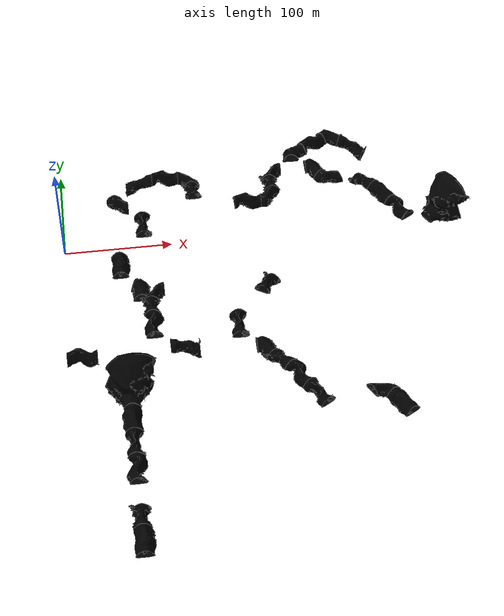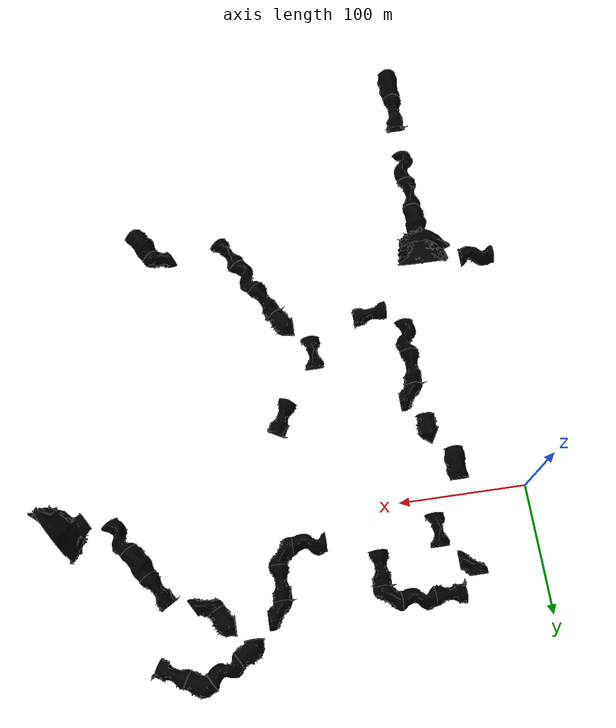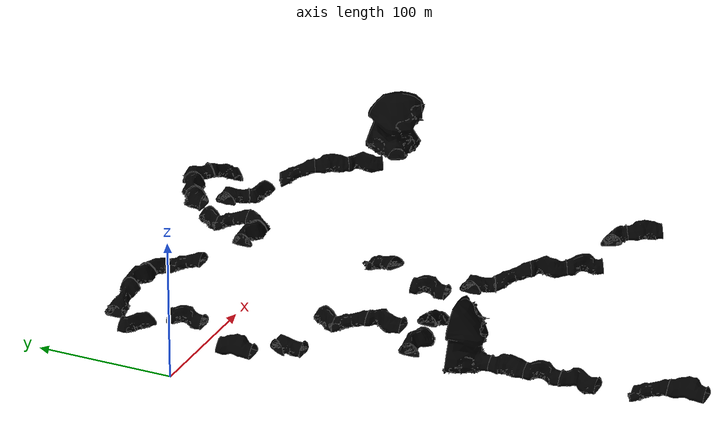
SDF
<sdf version="1.6">
 <world name="cave_qual">
  <physics name="1ms" type="ode">
   <max_step_size>0.004</max_step_size>
   <real_time_factor>1.0</real_time_factor>
  </physics>
  <scene>
   <ambient>0.1 0.1 0.1 1.0</ambient>
   <background>0 0 0 1.0</background>
   <grid>false</grid>
   <origin_visual>false</origin_visual>
  </scene>
  <atmosphere type="adiabatic">
   <temperature>288</temperature>
   <temperature_gradient>0.3</temperature_gradient>
  </atmosphere>
  <include>
   <static>true</static>
   <name>tile_3</name>
   <pose>50 50 0 0 -0 -1.5708</pose>
   <uri>https://fuel.ignitionrobotics.org/1.0/OpenRobotics/models/Cave Corner 02 Type B</uri>
  </include>
  <include>
   <static>true</static>
   <name>tile_4</name>
   <pose>75 75 0 0 -0 1.5708</pose>
   <uri>https://fuel.ignitionrobotics.org/1.0/OpenRobotics/models/Cave Elevation Type B</uri>
  </include>
  <include>
   <static>true</static>
   <name>tile_6</name>
   <pose>75 25 0 0 -0 -3.14159</pose>
   <uri>https://fuel.ignitionrobotics.org/1.0/OpenRobotics/models/Cave Straight 02 Lights Type B</uri>
  </include>
  <include>
   <static>true</static>
   <name>tile_10</name>
   <pose>50 -200 30 0 -0 1.5708</pose>
   <uri>https://fuel.ignitionrobotics.org/1.0/OpenRobotics/models/Cave Cavern Split 02 Type B</uri>
  </include>
  <include>
   <static>true</static>
   <name>tile_12</name>
   <pose>100 75 10 0 -0 -1.5708</pose>
   <uri>https://fuel.ignitionrobotics.org/1.0/OpenRobotics/models/Cave Straight 03 Type B</uri>
  </include>
  <include>
   <static>true</static>
   <name>tile_14</name>
   <pose>200 25 20 0 0 -4e-06</pose>
   <uri>https://fuel.ignitionrobotics.org/1.0/OpenRobotics/models/Cave Corner 02 Type B</uri>
  </include>
  <include>
   <static>true</static>
   <name>tile_15</name>
   <pose>125 50 10 0 0 -4e-06</pose>
   <uri>https://fuel.ignitionrobotics.org/1.0/OpenRobotics/models/Cave Elevation Type B</uri>
  </include>
  <include>
   <static>true</static>
   <name>tile_23</name>
   <pose>181.25 -76.6747 10 0 0 -0.523594</pose>
   <uri>https://fuel.ignitionrobotics.org/1.0/OpenRobotics/models/Cave Elevation Lights Type B</uri>
  </include>
  <include>
   <static>true</static>
   <name>tile_27</name>
   <pose>75 -75 20 0 -0 -3.14159</pose>
   <uri>https://fuel.ignitionrobotics.org/1.0/OpenRobotics/models/Cave Corner 02 Lights Type B</uri>
  </include>
  <include>
   <static>true</static>
   <name>tile_28</name>
   <pose>75 -100 20 0 0 -4e-06</pose>
   <uri>https://fuel.ignitionrobotics.org/1.0/OpenRobotics/models/Cave Elevation Type B</uri>
  </include>
  <include>
   <static>true</static>
   <name>tile_29</name>
   <pose>75 -125 30 0 -0 -3.14159</pose>
   <uri>https://fuel.ignitionrobotics.org/1.0/OpenRobotics/models/Cave Straight 03 Type B</uri>
  </include>
  <include>
   <static>true</static>
   <name>tile_33</name>
   <pose>100 -150 20 0 -0 -1.5708</pose>
   <uri>https://fuel.ignitionrobotics.org/1.0/OpenRobotics/models/Cave Elevation Type B</uri>
  </include>
  <include>
   <static>true</static>
   <name>tile_35</name>
   <pose>150 -125 20 0 -0 -3.14159</pose>
   <uri>https://fuel.ignitionrobotics.org/1.0/OpenRobotics/models/Cave Straight 02 Type B</uri>
  </include>
  <include>
   <static>true</static>
   <name>tile_36</name>
   <pose>12.5 -175 55 0 -0 1.5708</pose>
   <uri>https://fuel.ignitionrobotics.org/1.0/OpenRobotics/models/Cave Straight 03 Type B</uri>
  </include>
  <include>
   <static>true</static>
   <name>tile_38</name>
   <pose>175 -150 20 0 -0 -3.14159</pose>
   <uri>https://fuel.ignitionrobotics.org/1.0/OpenRobotics/models/Cave Corner 30 D Type B</uri>
  </include>
  <include>
   <static>true</static>
   <name>tile_39</name>
   <pose>181.691 -172.824 20 0 -0 0.523596</pose>
   <uri>https://fuel.ignitionrobotics.org/1.0/OpenRobotics/models/Cave Elevation Type B</uri>
  </include>
  <include>
   <static>true</static>
   <name>tile_40</name>
   <pose>194.191 -194.475 30 0 -0 -2.618</pose>
   <uri>https://fuel.ignitionrobotics.org/1.0/OpenRobotics/models/Cave Straight 03 Type B</uri>
  </include>
  <include>
   <static>true</static>
   <name>tile_41</name>
   <pose>206.691 -216.126 30 0 -0 -2.61799</pose>
   <uri>https://fuel.ignitionrobotics.org/1.0/OpenRobotics/models/Cave Straight 02 Type B</uri>
  </include>
  <include>
   <static>true</static>
   <name>tile_43</name>
   <pose>262.493 -212.776 30 0 -0 2.0944</pose>
   <uri>https://fuel.ignitionrobotics.org/1.0/OpenRobotics/models/Cave Corner 02 Type B</uri>
  </include>
  <include>
   <static>true</static>
   <name>tile_45</name>
   <pose>274.993 -234.427 30 0 -0 0.523596</pose>
   <uri>https://fuel.ignitionrobotics.org/1.0/OpenRobotics/models/Cave Straight 04 Type B</uri>
  </include>
  <include>
   <static>true</static>
   <name>tile_46</name>
   <pose>50 -225 30 0 0 -4e-06</pose>
   <uri>https://fuel.ignitionrobotics.org/1.0/OpenRobotics/models/Cave Straight 04 Type B</uri>
  </include>
  <include>
   <static>true</static>
   <name>tile_47</name>
   <pose>50 -250 30 0 -0 -3.14159</pose>
   <uri>https://fuel.ignitionrobotics.org/1.0/OpenRobotics/models/Cave Straight 02 Type B</uri>
  </include>
  <include>
   <static>true</static>
   <name>tile_48</name>
   <pose>50 -350 40 0 -0 -3.14159</pose>
   <uri>https://fuel.ignitionrobotics.org/1.0/OpenRobotics/models/Cave Straight 04 Type B</uri>
  </include>
  <include>
   <static>true</static>
   <name>tile_50</name>
   <pose>50 -275 30 0 0 -4e-06</pose>
   <uri>https://fuel.ignitionrobotics.org/1.0/OpenRobotics/models/Cave Straight 03 Type B</uri>
  </include>
  <include>
   <static>true</static>
   <name>tile_51</name>
   <pose>50 -325 30 0 0 -4e-06</pose>
   <uri>https://fuel.ignitionrobotics.org/1.0/OpenRobotics/models/Cave Elevation Type B</uri>
  </include>
  <include>
   <static>true</static>
   <name>tile_53</name>
   <pose>175 25 20 0 -0 -1.5708</pose>
   <uri>https://fuel.ignitionrobotics.org/1.0/OpenRobotics/models/Cave Straight 03 Type B</uri>
  </include>
  <include>
   <static>true</static>
   <name>tile_54</name>
   <pose>200 75 10 0 -0 -3.14159</pose>
   <uri>https://fuel.ignitionrobotics.org/1.0/OpenRobotics/models/Cave Corner 02 Type B</uri>
  </include>
  <include>
   <static>true</static>
   <name>tile_55</name>
   <pose>125 75 10 0 -0 1.5708</pose>
   <uri>https://fuel.ignitionrobotics.org/1.0/OpenRobotics/models/Cave Corner 02 Type B</uri>
  </include>
  <include>
   <static>true</static>
   <name>tile_56</name>
   <pose>200 50 10 0 0 -4e-06</pose>
   <uri>https://fuel.ignitionrobotics.org/1.0/OpenRobotics/models/Cave Elevation Type B</uri>
  </include>
  <include>
   <static>true</static>
   <name>tile_58</name>
   <pose>225 100 10 0 0 -1.57079</pose>
   <uri>https://fuel.ignitionrobotics.org/1.0/OpenRobotics/models/Cave Corner 30 D Type B</uri>
  </include>
  <include>
   <static>true</static>
   <name>tile_59</name>
   <pose>248.325 106.25 9.99999 0 0 -1.04719</pose>
   <uri>https://fuel.ignitionrobotics.org/1.0/OpenRobotics/models/Cave Straight 03 Type B</uri>
  </include>
  <include>
   <static>true</static>
   <name>tile_60</name>
   <pose>269.976 118.75 9.99999 0 -0 -2.61799</pose>
   <uri>https://fuel.ignitionrobotics.org/1.0/OpenRobotics/models/Cave Corner 30 D Type B</uri>
  </include>
  <include>
   <static>true</static>
   <name>tile_61</name>
   <pose>287.051 101.675 0 0 -0 -2.0944</pose>
   <uri>https://fuel.ignitionrobotics.org/1.0/OpenRobotics/models/Cave Elevation Type B</uri>
  </include>
  <include>
   <static>true</static>
   <name>tile_62</name>
   <pose>250 75 10 0 -0 -3.14159</pose>
   <uri>https://fuel.ignitionrobotics.org/1.0/OpenRobotics/models/Cave Corner 30 D Type B</uri>
  </include>
  <include>
   <static>true</static>
   <name>tile_64</name>
   <pose>256.25 51.6747 10 0 0 -1.04719</pose>
   <uri>https://fuel.ignitionrobotics.org/1.0/OpenRobotics/models/Cave Corner 02 Type B</uri>
  </include>
  <include>
   <static>true</static>
   <name>tile_65</name>
   <pose>290.401 42.5241 10 0 -0 0.523596</pose>
   <uri>https://fuel.ignitionrobotics.org/1.0/OpenRobotics/models/Cave Elevation Type B</uri>
  </include>
  <include>
   <static>true</static>
   <name>tile_66</name>
   <pose>315.401 -0.777207 20 0 -0 -2.618</pose>
   <uri>https://fuel.ignitionrobotics.org/1.0/OpenRobotics/models/Cave Straight 03 Type B</uri>
  </include>
  <include>
   <static>true</static>
   <name>tile_67</name>
   <pose>302.901 20.8734 20 0 -0 0.523596</pose>
   <uri>https://fuel.ignitionrobotics.org/1.0/OpenRobotics/models/Cave Straight 04 Type B</uri>
  </include>
  <include>
   <static>true</static>
   <name>tile_70</name>
   <pose>349.551 -9.92784 20 0 -0 0.523599</pose>
   <uri>https://fuel.ignitionrobotics.org/1.0/OpenRobotics/models/Cave Cavern Split 02 Type B</uri>
  </include>
  <include>
   <static>true</static>
   <name>tile_72</name>
   <pose>50 -25 0 0 -0 -3.14159</pose>
   <uri>https://fuel.ignitionrobotics.org/1.0/OpenRobotics/models/Cave Straight 04 Lights Type B</uri>
  </include>
  <include>
   <static>true</static>
   <name>tile_75</name>
   <pose>73.3253 -56.25 4e-06 0 -0 2.618</pose>
   <uri>https://fuel.ignitionrobotics.org/1.0/OpenRobotics/models/Cave Corner 30 D Lights Type B</uri>
  </include>
  <wind><linear_velocity>0.000000 0.000000 0.000000</linear_velocity></wind>
  <plugin name="ignition::gazebo::systems::WindEffects" filename="libignition-gazebo-wind-effects-system.so">
   <horizontal>
    <magnitude>
     <time_for_rise>10</time_for_rise>
     <sin><amplitude_percent>0.05</amplitude_percent><period>60</period></sin>
     <noise type="gaussian"><mean>0</mean><stddev>0.0002</stddev></noise>
    </magnitude>
    <direction>
     <time_for_rise>30</time_for_rise>
     <sin><amplitude>5</amplitude><period>20</period></sin>
     <noise type="gaussian"><mean>0</mean><stddev>0.03</stddev></noise>
    </direction>
   </horizontal>
   <vertical><noise type="gaussian"><mean>0</mean><stddev>0.03</stddev></noise></vertical>
  </plugin>
 </world>
</sdf>

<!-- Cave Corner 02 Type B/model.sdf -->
<sdf version="1.6">
  <model name="Cave Corner 02 Type B">
    <static>true</static>
    <link name="base_link">
      <collision name="collision">
        <pose>0 0 0 0 0 0</pose>
        <geometry>
          <mesh>
            <uri>model://cave_corner_02/meshes/cavecorner02.dae</uri>
            <scale>1.005 1.005 1.0</scale>
          </mesh>
        </geometry>
      </collision>
      <visual name="CaveWall_visual">
        <geometry>
          <mesh>
            <uri>model://cave_corner_02/meshes/cavecorner02.dae</uri>
            <submesh>
              <name>CaveWall</name>
              <center>false</center>
            </submesh>
            <scale>1.005 1.005 1.0</scale>
          </mesh>
        </geometry>
        <material>
          <diffuse>0 0 0 1</diffuse>
          <specular>0 0 0 1</specular>
          <pbr>
            <metal>
              <albedo_map>model://cave_corner_02/materials/textures/CaveWall_Albedo.png</albedo_map>
              <normal_map>model://cave_corner_02/materials/textures/CaveWall_Normal.png</normal_map>
              <roughness_map>model://cave_corner_02/materials/textures/CaveWall_Roughness.png</roughness_map>
            </metal>
          </pbr>

          <script>
            <uri>model://cave_corner_02/materials/scripts/</uri>
            <uri>model://cave_corner_02/materials/textures/</uri>
            <name>CaveTile/CaveWall_Diffuse</name>
          </script>
        </material>
      </visual>
      <visual name="StriatedRock_visual">
        <geometry>
          <mesh>
            <uri>model://cave_corner_02/meshes/cavecorner02.dae</uri>
            <submesh>
              <name>StriatedRock</name>
              <center>false</center>
            </submesh>
            <scale>1.005 1.005 1.0</scale>
          </mesh>
        </geometry>
        <material>
          <diffuse>0 0 0 1</diffuse>
          <specular>0 0 0 1</specular>
          <pbr>
            <metal>
              <albedo_map>model://cave_corner_02/materials/textures/StriatedRock_Albedo.png</albedo_map>
              <normal_map>model://cave_corner_02/materials/textures/StriatedRock_Normal.png</normal_map>
              <roughness_map>model://cave_corner_02/materials/textures/StriatedRock_Roughness.png</roughness_map>
            </metal>
          </pbr>

          <script>
            <uri>model://cave_corner_02/materials/scripts/</uri>
            <uri>model://cave_corner_02/materials/textures/</uri>
            <name>CaveTile/StriatedRock_Diffuse</name>
          </script>
        </material>
      </visual>
      <visual name="RockPile_visual">
        <geometry>
          <mesh>
            <uri>model://cave_corner_02/meshes/cavecorner02.dae</uri>
            <submesh>
              <name>RockPile</name>
              <center>false</center>
            </submesh>
            <scale>1.005 1.005 1.0</scale>
          </mesh>
        </geometry>
        <material>
          <diffuse>0 0 0 1</diffuse>
          <specular>0 0 0 1</specular>
          <pbr>
            <metal>
              <albedo_map>model://cave_corner_02/materials/textures/RockPile_Albedo.png</albedo_map>
              <normal_map>model://cave_corner_02/materials/textures/RockPile_Normal.png</normal_map>
              <roughness_map>model://cave_corner_02/materials/textures/RockPile_Roughness.png</roughness_map>
            </metal>
          </pbr>

          <script>
            <uri>model://cave_corner_02/materials/scripts/</uri>
            <uri>model://cave_corner_02/materials/textures/</uri>
            <name>CaveTile/RockPile_Diffuse</name>
          </script>
        </material>
      </visual>
    </link>
  </model>
</sdf>

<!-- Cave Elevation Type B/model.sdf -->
<sdf version="1.6">
  <model name="Cave Elevation Type B">
    <static>true</static>
    <link name="base_link">
      <collision name="collision">
        <pose>0 0 0 0 0 0</pose>
        <geometry>
          <mesh>
            <uri>model://Cave Elevation Type B/meshes/caveelevation.dae</uri>
            <scale>1.0 1.0 1.0</scale>
          </mesh>
        </geometry>
      </collision>
      <visual name="CaveWall_visual">
        <geometry>
          <mesh>
            <uri>model://Cave Elevation Type B/meshes/caveelevation.dae</uri>
            <submesh>
              <name>CaveWall</name>
              <center>false</center>
            </submesh>
          </mesh>
        </geometry>
        <material>
          <diffuse>0 0 0 1</diffuse>
          <specular>0 0 0 1</specular>
          <pbr>
            <metal>
              <albedo_map>model://Cave Elevation Type B/materials/textures/CaveWall_Albedo.png</albedo_map>
              <normal_map>model://Cave Elevation Type B/materials/textures/CaveWall_Normal.png</normal_map>
              <roughness_map>model://Cave Elevation Type B/materials/textures/CaveWall_Roughness.png</roughness_map>
            </metal>
          </pbr>

          <script>
            <uri>model://Cave Elevation Type B/materials/scripts/</uri>
            <uri>model://Cave Elevation Type B/materials/textures/</uri>
            <name>CaveTile/CaveWall_Diffuse</name>
          </script>
        </material>
      </visual>
      <visual name="RockPile_visual">
        <geometry>
          <mesh>
            <uri>model://Cave Elevation Type B/meshes/caveelevation.dae</uri>
            <submesh>
              <name>RockPile</name>
              <center>false</center>
            </submesh>
          </mesh>
        </geometry>
        <material>
          <diffuse>0 0 0 1</diffuse>
          <specular>0 0 0 1</specular>
          <pbr>
            <metal>
              <albedo_map>model://Cave Elevation Type B/materials/textures/RockPile_Albedo.png</albedo_map>
              <normal_map>model://Cave Elevation Type B/materials/textures/RockPile_Normal.png</normal_map>
              <roughness_map>model://Cave Elevation Type B/materials/textures/RockPile_Roughness.png</roughness_map>
            </metal>
          </pbr>

          <script>
            <uri>model://Cave Elevation Type B/materials/scripts/</uri>
            <uri>model://Cave Elevation Type B/materials/textures/</uri>
            <name>CaveTile/RockPile_Diffuse</name>
          </script>
        </material>
      </visual>
      <visual name="StriatedRock_visual">
        <geometry>
          <mesh>
            <uri>model://Cave Elevation Type B/meshes/caveelevation.dae</uri>
            <submesh>
              <name>StriatedRock</name>
              <center>false</center>
            </submesh>
          </mesh>
        </geometry>
        <material>
          <diffuse>0 0 0 1</diffuse>
          <specular>0 0 0 1</specular>
          <pbr>
            <metal>
              <albedo_map>model://Cave Elevation Type B/materials/textures/StriatedRock_Albedo.png</albedo_map>
              <normal_map>model://Cave Elevation Type B/materials/textures/StriatedRock_Normal.png</normal_map>
              <roughness_map>model://Cave Elevation Type B/materials/textures/StriatedRock_Roughness.png</roughness_map>
            </metal>
          </pbr>

          <script>
            <uri>model://Cave Elevation Type B/materials/scripts/</uri>
            <uri>model://Cave Elevation Type B/materials/textures/</uri>
            <name>CaveTile/StriatedRock_Diffuse</name>
          </script>
        </material>
      </visual>
    </link>

    <plugin filename="libignition-gazebo-performer-detector-system.so" name="ignition::gazebo::systems::PerformerDetector">
      <topic>/subt_performer_detector</topic>
      <pose>0 0 10 0 0 0</pose>
      <geometry>
        <box>
          <size>20 30 20</size>
        </box>
      </geometry>
      <header_data>
        <key>type</key>
        <value>elevation</value>
      </header_data>
    </plugin>
  </model>
</sdf>

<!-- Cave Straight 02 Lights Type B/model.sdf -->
<sdf version="1.6">
  <model name="Cave Straight 02 Lights Type B">
    <include>
      <name>cave_straight_02</name>
      <uri>model://Cave Straight 02 Type B</uri>
    </include>
    <static>true</static>
    <link name="lights">
      <light name="spot_light1" type="spot">
        <pose>0 5.0 3.5 0 0 0</pose>
        <diffuse>0 0 0 1</diffuse>
        <specular>0 0 0 1</specular>
        <attenuation>
          <range>20</range>
          <linear>0.2</linear>
          <constant>0.5</constant>
          <quadratic>0.02</quadratic>
        </attenuation>
        <spot>
          <inner_angle>2.0</inner_angle>
          <outer_angle>3.1</outer_angle>
          <falloff>1.0</falloff>
        </spot>
        <cast_shadows>false</cast_shadows>
      </light>

      <light name="spot_light2" type="spot">
        <pose>0 -5.5 4.5 0 0 0</pose>
        <diffuse>0 0 0 1</diffuse>
        <specular>0 0 0 1</specular>
        <attenuation>
          <range>20</range>
          <linear>0.2</linear>
          <constant>0.5</constant>
          <quadratic>0.02</quadratic>
        </attenuation>
        <spot>
          <inner_angle>2.0</inner_angle>
          <outer_angle>3.1</outer_angle>
          <falloff>1.0</falloff>
        </spot>
        <cast_shadows>false</cast_shadows>
      </light>
    </link>
  </model>
</sdf>

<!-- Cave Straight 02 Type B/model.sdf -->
<sdf version="1.6">
  <model name="Cave Straight 02 Type B">
    <static>true</static>
    <link name="base_link">
      <collision name="collision">
        <pose>0 0 0 0 0 0</pose>
        <geometry>
          <mesh>
            <uri>model://Cave Straight 02 Type B/meshes/cavestraight02.dae</uri>
            <scale>1.005 1.005 1.0</scale>
          </mesh>
        </geometry>
      </collision>
      <visual name="StriatedRock_visual">
        <geometry>
          <mesh>
            <uri>model://Cave Straight 02 Type B/meshes/cavestraight02.dae</uri>
            <scale>1.005 1.005 1.0</scale>
            <submesh>
              <name>StriatedRock</name>
              <center>false</center>
            </submesh>
          </mesh>
        </geometry>
        <material>
          <diffuse>0 0 0 1</diffuse>
          <specular>0 0 0 1</specular>
          <pbr>
            <metal>
              <albedo_map>model://Cave Straight 02 Type B/materials/textures/StriatedRock_Albedo.png</albedo_map>
              <normal_map>model://Cave Straight 02 Type B/materials/textures/StriatedRock_Normal.png</normal_map>
              <roughness_map>model://Cave Straight 02 Type B/materials/textures/StriatedRock_Roughness.png</roughness_map>
            </metal>
          </pbr>

          <script>
            <uri>model://Cave Straight 02 Type B/materials/scripts/</uri>
            <uri>model://Cave Straight 02 Type B/materials/textures/</uri>
            <name>CaveTile/StriatedRock_Diffuse</name>
          </script>
        </material>
      </visual>
      <visual name="RockPile_visual">
        <geometry>
          <mesh>
            <uri>model://Cave Straight 02 Type B/meshes/cavestraight02.dae</uri>
            <scale>1.005 1.005 1.0</scale>
            <submesh>
              <name>RockPile</name>
              <center>false</center>
            </submesh>
          </mesh>
        </geometry>
        <material>
          <diffuse>0 0 0 1</diffuse>
          <specular>0 0 0 1</specular>
          <pbr>
            <metal>
              <albedo_map>model://Cave Straight 02 Type B/materials/textures/RockPile_Albedo.png</albedo_map>
              <normal_map>model://Cave Straight 02 Type B/materials/textures/RockPile_Normal.png</normal_map>
              <roughness_map>model://Cave Straight 02 Type B/materials/textures/RockPile_Roughness.png</roughness_map>
            </metal>
          </pbr>

          <script>
            <uri>model://Cave Straight 02 Type B/materials/scripts/</uri>
            <uri>model://Cave Straight 02 Type B/materials/textures/</uri>
            <name>CaveTile/RockPile_Diffuse</name>
          </script>
        </material>
      </visual>
      <visual name="CaveWall_visual">
        <geometry>
          <mesh>
            <uri>model://Cave Straight 02 Type B/meshes/cavestraight02.dae</uri>
            <scale>1.005 1.005 1.0</scale>
            <submesh>
              <name>CaveWall</name>
              <center>false</center>
            </submesh>
          </mesh>
        </geometry>
        <material>
          <diffuse>0 0 0 1</diffuse>
          <specular>0 0 0 1</specular>
          <pbr>
            <metal>
              <albedo_map>model://Cave Straight 02 Type B/materials/textures/CaveWall_Albedo.png</albedo_map>
              <normal_map>model://Cave Straight 02 Type B/materials/textures/CaveWall_Normal.png</normal_map>
              <roughness_map>model://Cave Straight 02 Type B/materials/textures/CaveWall_Roughness.png</roughness_map>
            </metal>
          </pbr>

          <script>
            <uri>model://Cave Straight 02 Type B/materials/scripts/</uri>
            <uri>model://Cave Straight 02 Type B/materials/textures/</uri>
            <name>CaveTile/CaveWall_Diffuse</name>
          </script>
        </material>
      </visual>
    </link>
  </model>
</sdf>

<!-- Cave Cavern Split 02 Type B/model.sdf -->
<sdf version="1.6">
  <model name="Cave Cavern Split 02 Type B">
    <static>true</static>
    <link name="base_link">
      <collision name="collision">
        <pose>0 0 0 0 0 0</pose>
        <geometry>
          <mesh>
            <uri>model://cave_Cave Cavern Split 02 Type B/meshes/cavernsplit02.dae</uri>
            <scale>1.0 1.0 1.0</scale>
          </mesh>
        </geometry>
      </collision>
      <visual name="StriatedRock_visual">
        <geometry>
          <mesh>
            <uri>model://cave_Cave Cavern Split 02 Type B/meshes/cavernsplit02.dae</uri>
            <submesh>
              <name>StriatedRock</name>
              <center>false</center>
            </submesh>
          </mesh>
        </geometry>
        <material>
          <diffuse>0 0 0 1</diffuse>
          <specular>0 0 0 1</specular>
          <pbr>
            <metal>
              <albedo_map>model://cave_Cave Cavern Split 02 Type B/materials/textures/StriatedRock_Albedo.png</albedo_map>
              <normal_map>model://cave_Cave Cavern Split 02 Type B/materials/textures/StriatedRock_Normal.png</normal_map>
              <roughness_map>model://cave_Cave Cavern Split 02 Type B/materials/textures/StriatedRock_Roughness.png</roughness_map>
            </metal>
          </pbr>

          <script>
            <uri>model://cave_Cave Cavern Split 02 Type B/materials/scripts/</uri>
            <uri>model://cave_Cave Cavern Split 02 Type B/materials/textures/</uri>
            <name>CaveTile/StriatedRock_Diffuse</name>
          </script>
        </material>
      </visual>
      <visual name="RockPile_visual">
        <geometry>
          <mesh>
            <uri>model://cave_Cave Cavern Split 02 Type B/meshes/cavernsplit02.dae</uri>
            <submesh>
              <name>RockPile</name>
              <center>false</center>
            </submesh>
          </mesh>
        </geometry>
        <material>
          <diffuse>0 0 0 1</diffuse>
          <specular>0 0 0 1</specular>
          <pbr>
            <metal>
              <albedo_map>model://cave_Cave Cavern Split 02 Type B/materials/textures/RockPile_Albedo.png</albedo_map>
              <normal_map>model://cave_Cave Cavern Split 02 Type B/materials/textures/RockPile_Normal.png</normal_map>
              <roughness_map>model://cave_Cave Cavern Split 02 Type B/materials/textures/RockPile_Roughness.png</roughness_map>
            </metal>
          </pbr>

          <script>
            <uri>model://cave_Cave Cavern Split 02 Type B/materials/scripts/</uri>
            <uri>model://cave_Cave Cavern Split 02 Type B/materials/textures/</uri>
            <name>CaveTile/RockPile_Diffuse</name>
          </script>
        </material>
      </visual>
      <visual name="CaveWall_visual">
        <geometry>
          <mesh>
            <uri>model://cave_Cave Cavern Split 02 Type B/meshes/cavernsplit02.dae</uri>
            <submesh>
              <name>CaveWall_ncl1_1</name>
              <center>false</center>
            </submesh>
          </mesh>
        </geometry>
        <material>
          <diffuse>0 0 0 1</diffuse>
          <specular>0 0 0 1</specular>
          <pbr>
            <metal>
              <albedo_map>model://cave_Cave Cavern Split 02 Type B/materials/textures/CaveWall_Albedo.png</albedo_map>
              <normal_map>model://cave_Cave Cavern Split 02 Type B/materials/textures/CaveWall_Normal.png</normal_map>
              <roughness_map>model://cave_Cave Cavern Split 02 Type B/materials/textures/CaveWall_Roughness.png</roughness_map>
            </metal>
          </pbr>

          <script>
            <uri>model://cave_Cave Cavern Split 02 Type B/materials/scripts/</uri>
            <uri>model://cave_Cave Cavern Split 02 Type B/materials/textures/</uri>
            <name>CaveTile/CaveWall_Diffuse</name>
          </script>
        </material>
      </visual>
    </link>
  </model>
</sdf>

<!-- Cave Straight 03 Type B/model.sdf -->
<sdf version="1.6">
  <model name="Cave Straight 03 Type B">
    <static>true</static>
    <link name="base_link">
      <collision name="collision">
        <pose>0 0 0 0 0 0</pose>
        <geometry>
          <mesh>
            <uri>model://Cave Straight 03 Type B/meshes/cavestraight03.dae</uri>
            <scale>1.005 1.005 1.0</scale>
          </mesh>
        </geometry>
      </collision>
      <visual name="StriatedRock_visual">
        <geometry>
          <mesh>
            <uri>model://Cave Straight 03 Type B/meshes/cavestraight03.dae</uri>
            <submesh>
              <name>StriatedRock</name>
              <center>false</center>
            </submesh>
            <scale>1.005 1.005 1.0</scale>
          </mesh>
        </geometry>
        <material>
          <diffuse>0 0 0 1</diffuse>
          <specular>0 0 0 1</specular>
          <pbr>
            <metal>
              <albedo_map>model://Cave Straight 03 Type B/materials/textures/StriatedRock_Albedo.png</albedo_map>
              <normal_map>model://Cave Straight 03 Type B/materials/textures/StriatedRock_Normal.png</normal_map>
              <roughness_map>model://Cave Straight 03 Type B/materials/textures/StriatedRock_Roughness.png</roughness_map>
            </metal>
          </pbr>

          <script>
            <uri>model://Cave Straight 03 Type B/materials/scripts/</uri>
            <uri>model://Cave Straight 03 Type B/materials/textures/</uri>
            <name>CaveTile/StriatedRock_Diffuse</name>
          </script>
        </material>
      </visual>
      <visual name="RockPile_visual">
        <geometry>
          <mesh>
            <uri>model://Cave Straight 03 Type B/meshes/cavestraight03.dae</uri>
            <submesh>
              <name>RockPile</name>
              <center>false</center>
            </submesh>
            <scale>1.005 1.005 1.0</scale>
          </mesh>
        </geometry>
        <material>
          <diffuse>0 0 0 1</diffuse>
          <specular>0 0 0 1</specular>
          <pbr>
            <metal>
              <albedo_map>model://Cave Straight 03 Type B/materials/textures/RockPile_Albedo.png</albedo_map>
              <normal_map>model://Cave Straight 03 Type B/materials/textures/RockPile_Normal.png</normal_map>
              <roughness_map>model://Cave Straight 03 Type B/materials/textures/RockPile_Roughness.png</roughness_map>
            </metal>
          </pbr>

          <script>
            <uri>model://Cave Straight 03 Type B/materials/scripts/</uri>
            <uri>model://Cave Straight 03 Type B/materials/textures/</uri>
            <name>CaveTile/RockPile_Diffuse</name>
          </script>
        </material>
      </visual>
      <visual name="CaveWall_visual">
        <geometry>
          <mesh>
            <uri>model://Cave Straight 03 Type B/meshes/cavestraight03.dae</uri>
            <submesh>
              <name>CaveWall</name>
              <center>false</center>
            </submesh>
            <scale>1.005 1.005 1.0</scale>
          </mesh>
        </geometry>
        <material>
          <diffuse>0 0 0 1</diffuse>
          <specular>0 0 0 1</specular>
          <pbr>
            <metal>
              <albedo_map>model://Cave Straight 03 Type B/materials/textures/CaveWall_Albedo.png</albedo_map>
              <normal_map>model://Cave Straight 03 Type B/materials/textures/CaveWall_Normal.png</normal_map>
              <roughness_map>model://Cave Straight 03 Type B/materials/textures/CaveWall_Roughness.png</roughness_map>
            </metal>
          </pbr>

          <script>
            <uri>model://Cave Straight 03 Type B/materials/scripts/</uri>
            <uri>model://Cave Straight 03 Type B/materials/textures/</uri>
            <name>CaveTile/CaveWall_Diffuse</name>
          </script>
        </material>
      </visual>
    </link>
  </model>
</sdf>

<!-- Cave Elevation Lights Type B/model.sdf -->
<sdf version="1.6">
  <model name="Cave Elevation Lights Type B">
    <static>true</static>
    <include>
      <name>cave_elevation</name>
      <uri>model://Cave Elevation Type B</uri>
    </include>

    <link name="light1">
      <light name="spot_light1" type="spot">
        <pose>0 -8 17.5 0 0 0</pose>
        <diffuse>0 0 0 1</diffuse>
        <specular>0 0 0 1</specular>
        <attenuation>
          <range>20</range>
          <linear>0.2</linear>
          <constant>1.0</constant>
          <quadratic>0.01</quadratic>
        </attenuation>
        <spot>
          <inner_angle>2.0</inner_angle>
          <outer_angle>3.1</outer_angle>
          <falloff>1.2</falloff>
        </spot>
        <cast_shadows>false</cast_shadows>
      </light>

      <light name="spot_light2" type="spot">
        <pose>0 2 13.5 0 0 0</pose>
        <diffuse>0 0 0 1</diffuse>
        <specular>0 0 0 1</specular>
        <attenuation>
          <range>20</range>
          <linear>0.2</linear>
          <constant>1.0</constant>
          <quadratic>0.01</quadratic>
        </attenuation>
        <spot>
          <inner_angle>2.0</inner_angle>
          <outer_angle>3.1</outer_angle>
          <falloff>1.2</falloff>
        </spot>
        <cast_shadows>false</cast_shadows>
      </light>

      <light name="spot_light3" type="spot">
        <pose>0 12 9 0 0 0</pose>
        <diffuse>0 0 0 1</diffuse>
        <specular>0 0 0 1</specular>
        <attenuation>
          <range>20</range>
          <linear>0.2</linear>
          <constant>1.0</constant>
          <quadratic>0.01</quadratic>
        </attenuation>
        <spot>
          <inner_angle>2.0</inner_angle>
          <outer_angle>3.1</outer_angle>
          <falloff>1.2</falloff>
        </spot>
        <cast_shadows>false</cast_shadows>
      </light>
    </link>
  </model>
</sdf>

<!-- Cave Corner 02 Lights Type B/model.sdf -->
<sdf version="1.6">
  <model name="Cave Corner 02 Lights Type B">
    <include>
      <name>cave_corner_02</name>
      <uri>model://Cave Corner 02 Type B</uri>
    </include>
    <static>true</static>
    <link name="lights">
      <light name="spot_light1" type="spot">
        <pose>-2 6.0 3.5 0 0 0</pose>
        <diffuse>0 0 0 1</diffuse>
        <specular>0 0 0 1</specular>
        <attenuation>
          <range>20</range>
          <linear>0.2</linear>
          <constant>0.5</constant>
          <quadratic>0.02</quadratic>
        </attenuation>
        <spot>
          <inner_angle>2.0</inner_angle>
          <outer_angle>3.1</outer_angle>
          <falloff>1.0</falloff>
        </spot>
        <cast_shadows>false</cast_shadows>
      </light>

      <light name="spot_light2" type="spot">
        <pose>-6.5 -.25 4.5 0 0 0</pose>
        <diffuse>0 0 0 1</diffuse>
        <specular>0 0 0 1</specular>
        <attenuation>
          <range>20</range>
          <linear>0.2</linear>
          <constant>0.5</constant>
          <quadratic>0.02</quadratic>
        </attenuation>
        <spot>
          <inner_angle>2.0</inner_angle>
          <outer_angle>3.1</outer_angle>
          <falloff>1.0</falloff>
        </spot>
        <cast_shadows>false</cast_shadows>
      </light>
    </link>
  </model>
</sdf>

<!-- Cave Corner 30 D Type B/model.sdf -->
<sdf version="1.6">
  <model name="Cave Corner 30 D Type B">
    <static>true</static>
    <link name="base_link">
      <collision name="collision">
        <pose>0 0 0 0 0 0</pose>
        <geometry>
          <mesh>
            <uri>meshes/corner30deg.dae</uri>
            <scale>1.0 1.0 1.0</scale>
          </mesh>
        </geometry>
      </collision>
      <visual name="CaveWall_visual">
        <geometry>
          <mesh>
            <submesh>
              <name>CaveWall</name>
              <center>false</center>
            </submesh>
            <uri>meshes/corner30deg.dae</uri>
            <scale>1.0 1.0 1.0</scale>
          </mesh>
        </geometry>
        <material>
          <diffuse>0 0 0 1</diffuse>
          <specular>0 0 0 1</specular>
          <pbr>
            <metal>
              <albedo_map>model://Cave Corner 30 D Type B/materials/textures/CaveWall_Albedo.png</albedo_map>
              <normal_map>model://Cave Corner 30 D Type B/materials/textures/CaveWall_Normal.png</normal_map>
              <roughness_map>model://Cave Corner 30 D Type B/materials/textures/CaveWall_Roughness.png</roughness_map>
            </metal>
          </pbr>

          <script>
            <uri>materials/scripts/</uri>
            <uri>materials/textures/</uri>
            <name>CaveTile/CaveWall_Diffuse</name>
          </script>
        </material>
      </visual>
      <visual name="StriatedRock_visual">
        <geometry>
          <mesh>
            <uri>meshes/corner30deg.dae</uri>
            <submesh>
              <name>StriatedRock</name>
              <center>false</center>
            </submesh>
            <scale>1.0 1.0 1.0</scale>
          </mesh>
        </geometry>
        <material>
          <diffuse>0 0 0 1</diffuse>
          <specular>0 0 0 1</specular>
          <pbr>
            <metal>
              <albedo_map>model://Cave Corner 30 D Type B/materials/textures/StriatedRock_Albedo.png</albedo_map>
              <normal_map>model://Cave Corner 30 D Type B/materials/textures/StriatedRock_Normal.png</normal_map>
              <roughness_map>model://Cave Corner 30 D Type B/materials/textures/StriatedRock_Roughness.png</roughness_map>
            </metal>
          </pbr>

          <script>
            <uri>materials/scripts/</uri>
            <uri>materials/textures/</uri>
            <name>CaveTile/StriatedRock_Diffuse</name>
          </script>
        </material>
      </visual>
      <visual name="RockPile_visual">
        <geometry>
          <mesh>
            <uri>meshes/corner30deg.dae</uri>
            <submesh>
              <name>RockPile</name>
              <center>false</center>
            </submesh>
            <scale>1.0 1.0 1.0</scale>
          </mesh>
        </geometry>
        <material>
          <diffuse>0 0 0 1</diffuse>
          <specular>0 0 0 1</specular>
          <pbr>
            <metal>
              <albedo_map>model://Cave Corner 30 D Type B/materials/textures/RockPile_Albedo.png</albedo_map>
              <normal_map>model://Cave Corner 30 D Type B/materials/textures/RockPile_Normal.png</normal_map>
              <roughness_map>model://Cave Corner 30 D Type B/materials/textures/RockPile_Roughness.png</roughness_map>
            </metal>
          </pbr>

          <script>
            <uri>materials/scripts/</uri>
            <uri>materials/textures/</uri>
            <name>CaveTile/RockPile_Diffuse</name>
          </script>
        </material>
      </visual>

    </link>
  </model>
</sdf>

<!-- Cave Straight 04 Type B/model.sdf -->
<sdf version="1.6">
  <model name="Cave Straight 04 Type B">
    <static>true</static>
    <link name="base_link">
      <collision name="collision">
        <pose>0 0 0 0 0 0</pose>
        <geometry>
          <mesh>
            <uri>model://Cave Straight 04 Type B/meshes/cavestraight04.dae</uri>
            <scale>1.0 1.0 1.0</scale>
          </mesh>
        </geometry>
      </collision>
      <visual name="StriatedRock_visual">
        <geometry>
          <mesh>
            <uri>model://Cave Straight 04 Type B/meshes/cavestraight04.dae</uri>
            <submesh>
              <name>StriatedRock</name>
              <center>false</center>
            </submesh>
          </mesh>
        </geometry>
        <material>
          <diffuse>0 0 0 1</diffuse>
          <specular>0 0 0 1</specular>
          <pbr>
            <metal>
              <albedo_map>model://Cave Straight 04 Type B/materials/textures/StriatedRock_Albedo.png</albedo_map>
              <normal_map>model://Cave Straight 04 Type B/materials/textures/StriatedRock_Normal.png</normal_map>
              <roughness_map>model://Cave Straight 04 Type B/materials/textures/StriatedRock_Roughness.png</roughness_map>
            </metal>
          </pbr>

          <script>
            <uri>model://Cave Straight 04 Type B/materials/scripts/</uri>
            <uri>model://Cave Straight 04 Type B/materials/textures/</uri>
            <name>CaveTile/StriatedRock_Diffuse</name>
          </script>
        </material>
      </visual>
      <visual name="RockPile_visual">
        <geometry>
          <mesh>
            <uri>model://Cave Straight 04 Type B/meshes/cavestraight04.dae</uri>
            <submesh>
              <name>RockPile</name>
              <center>false</center>
            </submesh>
          </mesh>
        </geometry>
        <material>
          <diffuse>0 0 0 1</diffuse>
          <specular>0 0 0 1</specular>
          <pbr>
            <metal>
              <albedo_map>model://Cave Straight 04 Type B/materials/textures/RockPile_Albedo.png</albedo_map>
              <normal_map>model://Cave Straight 04 Type B/materials/textures/RockPile_Normal.png</normal_map>
              <roughness_map>model://Cave Straight 04 Type B/materials/textures/RockPile_Roughness.png</roughness_map>
            </metal>
          </pbr>

          <script>
            <uri>model://Cave Straight 04 Type B/materials/scripts/</uri>
            <uri>model://Cave Straight 04 Type B/materials/textures/</uri>
            <name>CaveTile/RockPile_Diffuse</name>
          </script>
        </material>
      </visual>
      <visual name="CaveWall_visual">
        <geometry>
          <mesh>
            <uri>model://Cave Straight 04 Type B/meshes/cavestraight04.dae</uri>
            <submesh>
              <name>CaveWall</name>
              <center>false</center>
            </submesh>
          </mesh>
        </geometry>
        <material>
          <diffuse>0 0 0 1</diffuse>
          <specular>0 0 0 1</specular>
          <pbr>
            <metal>
              <albedo_map>model://Cave Straight 04 Type B/materials/textures/CaveWall_Albedo.png</albedo_map>
              <normal_map>model://Cave Straight 04 Type B/materials/textures/CaveWall_Normal.png</normal_map>
              <roughness_map>model://Cave Straight 04 Type B/materials/textures/CaveWall_Roughness.png</roughness_map>
            </metal>
          </pbr>

          <script>
            <uri>model://Cave Straight 04 Type B/materials/scripts/</uri>
            <uri>model://Cave Straight 04 Type B/materials/textures/</uri>
            <name>CaveTile/CaveWall_Diffuse</name>
          </script>
        </material>
      </visual>
    </link>
  </model>
</sdf>

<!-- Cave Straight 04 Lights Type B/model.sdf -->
<sdf version="1.6">
  <model name="Cave Straight 04 Lights Type B">
    <include>
      <name>cave_straight_04</name>
      <uri>model://Cave Straight 04 Type B</uri>
    </include>
    <static>true</static>
    <link name="lights">
      <light name="spot_light1" type="spot">
        <pose>0 8 8.0 0 0 0</pose>
        <diffuse>0 0 0 1</diffuse>
        <specular>0 0 0 1</specular>
        <attenuation>
          <range>20</range>
          <linear>0.2</linear>
          <constant>0.3</constant>
          <quadratic>0.01</quadratic>
        </attenuation>
        <spot>
          <inner_angle>2.0</inner_angle>
          <outer_angle>3.1</outer_angle>
          <falloff>0.6</falloff>
        </spot>
        <cast_shadows>false</cast_shadows>
      </light>

      <light name="spot_light2" type="spot">
        <pose>0 -6.0 4.5 0 0 0</pose>
        <diffuse>0 0 0 1</diffuse>
        <specular>0 0 0 1</specular>
        <attenuation>
          <range>20</range>
          <linear>0.2</linear>
          <constant>0.3</constant>
          <quadratic>0.01</quadratic>
        </attenuation>
        <spot>
          <inner_angle>2.0</inner_angle>
          <outer_angle>3.1</outer_angle>
          <falloff>0.6</falloff>
        </spot>
        <cast_shadows>false</cast_shadows>
      </light>
    </link>
  </model>
</sdf>

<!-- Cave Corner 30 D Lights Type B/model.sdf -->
<sdf version="1.6">
  <model name="Cave Corner 30 D Lights Type B">
    <include>
      <name>cave_corner_30_d</name>
      <uri>model://Cave Corner 30 D Type B</uri>
    </include>
    <static>true</static>
    <link name="lights">
      <light name="spot_light1" type="spot">
        <pose>1.75 6.0 3.5 0 0 0</pose>
        <diffuse>0 0 0 1</diffuse>
        <specular>0 0 0 1</specular>
        <attenuation>
          <range>20</range>
          <linear>0.2</linear>
          <constant>0.7</constant>
          <quadratic>0.02</quadratic>
        </attenuation>
        <spot>
          <inner_angle>2.0</inner_angle>
          <outer_angle>3.1</outer_angle>
          <falloff>1.0</falloff>
        </spot>
        <cast_shadows>false</cast_shadows>
      </light>

      <light name="spot_light2" type="spot">
        <pose>6.5 0 4.5 0 0 0</pose>
        <diffuse>0 0 0 1</diffuse>
        <specular>0 0 0 1</specular>
        <attenuation>
          <range>20</range>
          <linear>0.2</linear>
          <constant>0.7</constant>
          <quadratic>0.02</quadratic>
        </attenuation>
        <spot>
          <inner_angle>2.0</inner_angle>
          <outer_angle>3.1</outer_angle>
          <falloff>1.0</falloff>
        </spot>
        <cast_shadows>false</cast_shadows>
      </light>
    </link>
  </model>
</sdf>
